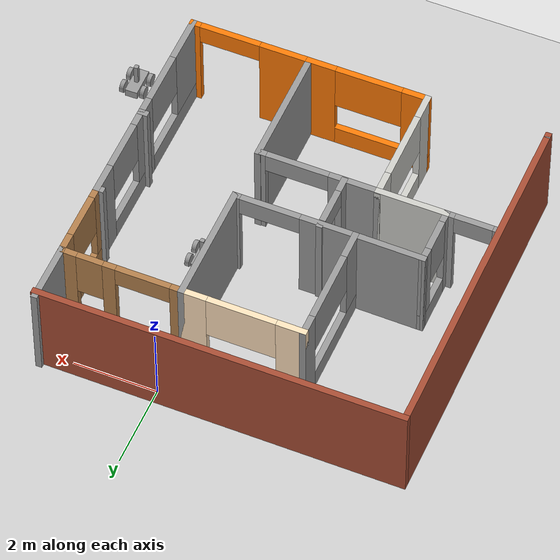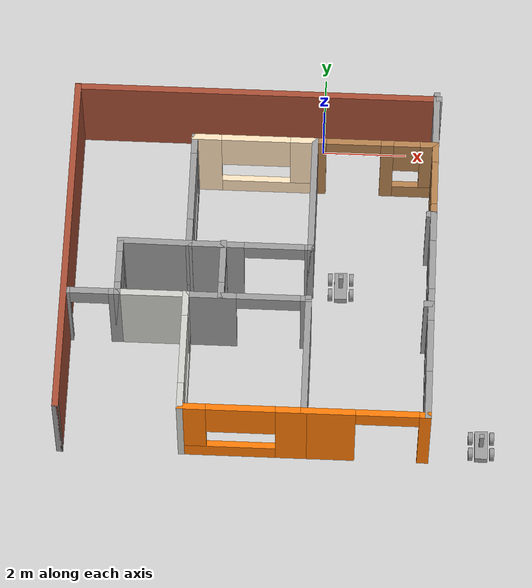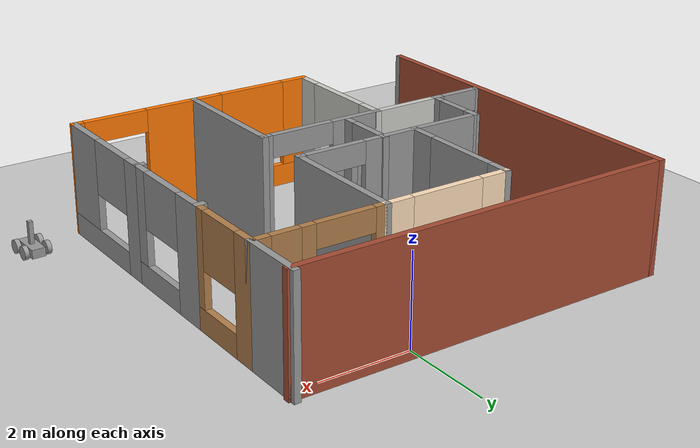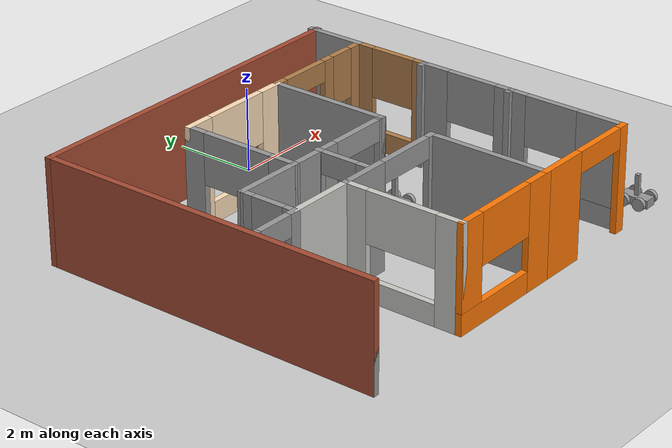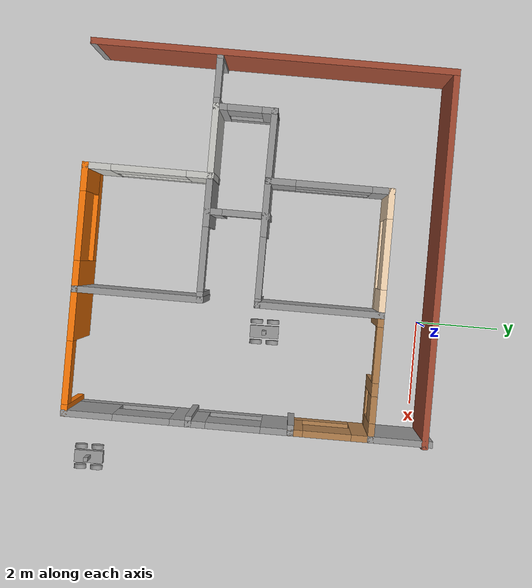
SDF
<sdf version="1.6">
 <world name="default">
  <plugin name="project_1_plugin" filename="libproject_1_plugin.so"/>
  <light name="sun" type="directional">
   <pose>0 0 10 0 -0 0</pose>
   <diffuse>0.8 0.8 0.8 1</diffuse>
   <specular>0.2 0.2 0.2 1</specular>
   <attenuation>
    <range>1000</range>
    <constant>0.9</constant>
    <linear>0.01</linear>
    <quadratic>0.001</quadratic>
   </attenuation>
   <direction>-0.5 0.1 -0.9</direction>
  </light>
  <model name="ground_plane">
   <static>1</static>
   <link name="link">
    <collision name="collision">
     <geometry><plane><normal>0 0 1</normal><size>100 100</size></plane></geometry>
     <surface>
      <contact><collide_bitmask>65535</collide_bitmask></contact>
      <friction><ode><mu>100</mu><mu2>50</mu2></ode></friction>
     </surface>
    </collision>
    <visual name="visual">
     <cast_shadows>0</cast_shadows>
     <geometry><plane><normal>0 0 1</normal><size>100 100</size></plane></geometry>
     <material>
      <script><uri>file://media/materials/scripts/gazebo.material</uri><name>Gazebo/Grey</name></script>
     </material>
    </visual>
   </link>
  </model>
  <gravity>0 0 -9.8</gravity>
  <magnetic_field>6e-06 2.3e-05 -4.2e-05</magnetic_field>
  <atmosphere type="adiabatic"/>
  <physics name="default_physics" default="0" type="ode">
   <max_step_size>0.001</max_step_size>
   <real_time_factor>1</real_time_factor>
   <real_time_update_rate>1000</real_time_update_rate>
  </physics>
  <scene><ambient>0.4 0.4 0.4 1</ambient><background>0.7 0.7 0.7 1</background><shadows>1</shadows></scene>
  <spherical_coordinates>
   <surface_model>EARTH_WGS84</surface_model>
   <latitude_deg>0</latitude_deg>
   <longitude_deg>0</longitude_deg>
   <elevation>0</elevation>
   <heading_deg>0</heading_deg>
  </spherical_coordinates>
  <model name="MyHome">
   <pose>-1.58 -3.915 0 0 -0 0</pose>
   <link name="Wall_0">
    <pose>-0.025 2.875 0 0 -0 0</pose>
    <visual name="Wall_0_Visual_0">
     <pose>-1.14611 0 1.25 0 -0 0</pose>
     <geometry><box><size>0.707769 0.15 2.5</size></box></geometry>
     <material>
      <script><uri>file://media/materials/scripts/gazebo.material</uri><name>Gazebo/Grey</name></script>
      <ambient>1 0.878431 0.733333 1</ambient>
     </material>
     <meta><layer>0</layer></meta>
    </visual>
    <collision name="Wall_0_Collision_0">
     <geometry><box><size>0.707769 0.15 2.5</size></box></geometry>
     <pose>-1.14611 0 1.25 0 -0 0</pose>
    </collision>
    <visual name="Wall_0_Visual_1">
     <pose>0.353885 0 0.25 0 -0 0</pose>
     <geometry><box><size>2.29223 0.15 0.5</size></box></geometry>
     <material>
      <script><uri>file://media/materials/scripts/gazebo.material</uri><name>Gazebo/Grey</name></script>
      <ambient>1 0.878431 0.733333 1</ambient>
     </material>
     <meta><layer>0</layer></meta>
    </visual>
    <collision name="Wall_0_Collision_1">
     <geometry><box><size>2.29223 0.15 0.5</size></box></geometry>
     <pose>0.353885 0 0.25 0 -0 0</pose>
    </collision>
    <visual name="Wall_0_Visual_2">
     <pose>1.16841 0 1.5 0 -0 0</pose>
     <geometry><box><size>0.663189 0.15 2</size></box></geometry>
     <material>
      <script><uri>file://media/materials/scripts/gazebo.material</uri><name>Gazebo/Grey</name></script>
      <ambient>1 0.878431 0.733333 1</ambient>
     </material>
     <meta><layer>0</layer></meta>
    </visual>
    <collision name="Wall_0_Collision_2">
     <geometry><box><size>0.663189 0.15 2</size></box></geometry>
     <pose>1.16841 0 1.5 0 -0 0</pose>
    </collision>
    <visual name="Wall_0_Visual_3">
     <pose>0.02229 0 1.9 0 -0 0</pose>
     <geometry><box><size>1.62904 0.15 1.2</size></box></geometry>
     <material>
      <script><uri>file://media/materials/scripts/gazebo.material</uri><name>Gazebo/Grey</name></script>
      <ambient>1 0.878431 0.733333 1</ambient>
     </material>
     <meta><layer>0</layer></meta>
    </visual>
    <collision name="Wall_0_Collision_3">
     <geometry><box><size>1.62904 0.15 1.2</size></box></geometry>
     <pose>0.02229 0 1.9 0 -0 0</pose>
    </collision>
   </link>
   <link name="Wall_11">
    <collision name="Wall_11_Collision">
     <geometry><box><size>0.25 0.15 2.5</size></box></geometry>
     <pose>0 0 1.25 0 -0 0</pose>
    </collision>
    <visual name="Wall_11_Visual">
     <pose>0 0 1.25 0 -0 0</pose>
     <geometry><box><size>0.25 0.15 2.5</size></box></geometry>
     <material>
      <script><uri>file://media/materials/scripts/gazebo.material</uri><name>Gazebo/Grey</name></script>
      <ambient>1 1 1 1</ambient>
     </material>
     <meta><layer>0</layer></meta>
    </visual>
    <pose>4.2 1.025 0 0 -0 3.14159</pose>
   </link>
   <link name="Wall_13">
    <pose>4.25 -0.15 0 0 0 -1.5708</pose>
    <visual name="Wall_13_Visual_0">
     <pose>-0.866536 0 1.25 0 -0 0</pose>
     <geometry><box><size>0.766927 0.15 2.5</size></box></geometry>
     <material>
      <script><uri>file://media/materials/scripts/gazebo.material</uri><name>Gazebo/Grey</name></script>
      <ambient>1 1 1 1</ambient>
     </material>
     <meta><layer>0</layer></meta>
    </visual>
    <collision name="Wall_13_Collision_0">
     <geometry><box><size>0.766927 0.15 2.5</size></box></geometry>
     <pose>-0.866536 0 1.25 0 -0 0</pose>
    </collision>
    <visual name="Wall_13_Visual_1">
     <pose>0.383464 0 0.25 0 -0 0</pose>
     <geometry><box><size>1.73307 0.15 0.5</size></box></geometry>
     <material>
      <script><uri>file://media/materials/scripts/gazebo.material</uri><name>Gazebo/Grey</name></script>
      <ambient>1 1 1 1</ambient>
     </material>
     <meta><layer>0</layer></meta>
    </visual>
    <collision name="Wall_13_Collision_1">
     <geometry><box><size>1.73307 0.15 0.5</size></box></geometry>
     <pose>0.383464 0 0.25 0 -0 0</pose>
    </collision>
    <visual name="Wall_13_Visual_2">
     <pose>1.01502 0 1.5 0 -0 0</pose>
     <geometry><box><size>0.469953 0.15 2</size></box></geometry>
     <material>
      <script><uri>file://media/materials/scripts/gazebo.material</uri><name>Gazebo/Grey</name></script>
      <ambient>1 1 1 1</ambient>
     </material>
     <meta><layer>0</layer></meta>
    </visual>
    <collision name="Wall_13_Collision_2">
     <geometry><box><size>0.469953 0.15 2</size></box></geometry>
     <pose>1.01502 0 1.5 0 -0 0</pose>
    </collision>
    <visual name="Wall_13_Visual_3">
     <pose>0.148487 0 1.9 0 -0 0</pose>
     <geometry><box><size>1.26312 0.15 1.2</size></box></geometry>
     <material>
      <script><uri>file://media/materials/scripts/gazebo.material</uri><name>Gazebo/Grey</name></script>
      <ambient>1 1 1 1</ambient>
     </material>
     <meta><layer>0</layer></meta>
    </visual>
    <collision name="Wall_13_Collision_3">
     <geometry><box><size>1.26312 0.15 1.2</size></box></geometry>
     <pose>0.148487 0 1.9 0 -0 0</pose>
    </collision>
   </link>
   <link name="Wall_14">
    <collision name="Wall_14_Collision">
     <geometry><box><size>0.25 0.15 2.5</size></box></geometry>
     <pose>0 0 1.25 0 -0 0</pose>
    </collision>
    <visual name="Wall_14_Visual">
     <pose>0 0 1.25 0 -0 0</pose>
     <geometry><box><size>0.25 0.15 2.5</size></box></geometry>
     <material>
      <script><uri>file://media/materials/scripts/gazebo.material</uri><name>Gazebo/Grey</name></script>
      <ambient>1 1 1 1</ambient>
     </material>
     <meta><layer>0</layer></meta>
    </visual>
    <pose>4.2 -1.325 0 0 -0 3.14159</pose>
   </link>
   <link name="Wall_16">
    <pose>4.25 -2.75 0 0 0 -1.5708</pose>
    <visual name="Wall_16_Visual_0">
     <pose>-1.24918 0 1.25 0 -0 0</pose>
     <geometry><box><size>0.501638 0.15 2.5</size></box></geometry>
     <material>
      <script><uri>file://media/materials/scripts/gazebo.material</uri><name>Gazebo/Grey</name></script>
      <ambient>1 1 1 1</ambient>
     </material>
     <meta><layer>0</layer></meta>
    </visual>
    <collision name="Wall_16_Collision_0">
     <geometry><box><size>0.501638 0.15 2.5</size></box></geometry>
     <pose>-1.24918 0 1.25 0 -0 0</pose>
    </collision>
    <visual name="Wall_16_Visual_1">
     <pose>0.250819 0 0.25 0 -0 0</pose>
     <geometry><box><size>2.49836 0.15 0.5</size></box></geometry>
     <material>
      <script><uri>file://media/materials/scripts/gazebo.material</uri><name>Gazebo/Grey</name></script>
      <ambient>1 1 1 1</ambient>
     </material>
     <meta><layer>0</layer></meta>
    </visual>
    <collision name="Wall_16_Collision_1">
     <geometry><box><size>2.49836 0.15 0.5</size></box></geometry>
     <pose>0.250819 0 0.25 0 -0 0</pose>
    </collision>
    <visual name="Wall_16_Visual_2">
     <pose>0.905819 0 1.5 0 -0 0</pose>
     <geometry><box><size>1.18836 0.15 2</size></box></geometry>
     <material>
      <script><uri>file://media/materials/scripts/gazebo.material</uri><name>Gazebo/Grey</name></script>
      <ambient>1 1 1 1</ambient>
     </material>
     <meta><layer>0</layer></meta>
    </visual>
    <collision name="Wall_16_Collision_2">
     <geometry><box><size>1.18836 0.15 2</size></box></geometry>
     <pose>0.905819 0 1.5 0 -0 0</pose>
    </collision>
    <visual name="Wall_16_Visual_3">
     <pose>-0.343362 0 1.9 0 -0 0</pose>
     <geometry><box><size>1.31 0.15 1.2</size></box></geometry>
     <material>
      <script><uri>file://media/materials/scripts/gazebo.material</uri><name>Gazebo/Grey</name></script>
      <ambient>1 1 1 1</ambient>
     </material>
     <meta><layer>0</layer></meta>
    </visual>
    <collision name="Wall_16_Collision_3">
     <geometry><box><size>1.31 0.15 1.2</size></box></geometry>
     <pose>-0.343362 0 1.9 0 -0 0</pose>
    </collision>
   </link>
   <link name="Wall_18">
    <pose>2.825 -4.175 0 0 -0 3.14159</pose>
    <visual name="Wall_18_Visual_0">
     <pose>-1.36366 0 1.25 0 -0 0</pose>
     <geometry><box><size>0.272669 0.15 2.5</size></box></geometry>
     <material>
      <script><uri>file://media/materials/scripts/gazebo.material</uri><name>Gazebo/Grey</name></script>
      <ambient>0.996078 0.47451 0.0196078 1</ambient>
     </material>
     <meta><layer>0</layer></meta>
    </visual>
    <collision name="Wall_18_Collision_0">
     <geometry><box><size>0.272669 0.15 2.5</size></box></geometry>
     <pose>-1.36366 0 1.25 0 -0 0</pose>
    </collision>
    <visual name="Wall_18_Visual_1">
     <pose>0.866335 0 1.25 0 -0 0</pose>
     <geometry><box><size>1.26733 0.15 2.5</size></box></geometry>
     <material>
      <script><uri>file://media/materials/scripts/gazebo.material</uri><name>Gazebo/Grey</name></script>
      <ambient>0.996078 0.47451 0.0196078 1</ambient>
     </material>
     <meta><layer>0</layer></meta>
    </visual>
    <collision name="Wall_18_Collision_1">
     <geometry><box><size>1.26733 0.15 2.5</size></box></geometry>
     <pose>0.866335 0 1.25 0 -0 0</pose>
    </collision>
    <visual name="Wall_18_Visual_2">
     <pose>-0.497331 0 2.25 0 -0 0</pose>
     <geometry><box><size>1.46 0.15 0.5</size></box></geometry>
     <material>
      <script><uri>file://media/materials/scripts/gazebo.material</uri><name>Gazebo/Grey</name></script>
      <ambient>0.996078 0.47451 0.0196078 1</ambient>
     </material>
     <meta><layer>0</layer></meta>
    </visual>
    <collision name="Wall_18_Collision_2">
     <geometry><box><size>1.46 0.15 0.5</size></box></geometry>
     <pose>-0.497331 0 2.25 0 -0 0</pose>
    </collision>
   </link>
   <link name="Wall_2">
    <pose>-1.45 1.45 0 0 0 -1.5708</pose>
    <visual name="Wall_2_Visual_0">
     <pose>-1.23642 0 1.25 0 -0 0</pose>
     <geometry><box><size>0.527169 0.15 2.5</size></box></geometry>
     <material>
      <script><uri>file://media/materials/scripts/gazebo.material</uri><name>Gazebo/Grey</name></script>
      <ambient>0.529412 0.529412 0.529412 1</ambient>
     </material>
     <meta><layer>0</layer></meta>
    </visual>
    <collision name="Wall_2_Collision_0">
     <geometry><box><size>0.527169 0.15 2.5</size></box></geometry>
     <pose>-1.23642 0 1.25 0 -0 0</pose>
    </collision>
    <visual name="Wall_2_Visual_1">
     <pose>0.263585 0 0.25 0 -0 0</pose>
     <geometry><box><size>2.47283 0.15 0.5</size></box></geometry>
     <material>
      <script><uri>file://media/materials/scripts/gazebo.material</uri><name>Gazebo/Grey</name></script>
      <ambient>0.529412 0.529412 0.529412 1</ambient>
     </material>
     <meta><layer>0</layer></meta>
    </visual>
    <collision name="Wall_2_Collision_1">
     <geometry><box><size>2.47283 0.15 0.5</size></box></geometry>
     <pose>0.263585 0 0.25 0 -0 0</pose>
    </collision>
    <visual name="Wall_2_Visual_2">
     <pose>1.14386 0 1.5 0 -0 0</pose>
     <geometry><box><size>0.712285 0.15 2</size></box></geometry>
     <material>
      <script><uri>file://media/materials/scripts/gazebo.material</uri><name>Gazebo/Grey</name></script>
      <ambient>0.529412 0.529412 0.529412 1</ambient>
     </material>
     <meta><layer>0</layer></meta>
    </visual>
    <collision name="Wall_2_Collision_2">
     <geometry><box><size>0.712285 0.15 2</size></box></geometry>
     <pose>1.14386 0 1.5 0 -0 0</pose>
    </collision>
    <visual name="Wall_2_Visual_3">
     <pose>-0.092558 0 1.9 0 -0 0</pose>
     <geometry><box><size>1.76055 0.15 1.2</size></box></geometry>
     <material>
      <script><uri>file://media/materials/scripts/gazebo.material</uri><name>Gazebo/Grey</name></script>
      <ambient>0.529412 0.529412 0.529412 1</ambient>
     </material>
     <meta><layer>0</layer></meta>
    </visual>
    <collision name="Wall_2_Collision_3">
     <geometry><box><size>1.76055 0.15 1.2</size></box></geometry>
     <pose>-0.092558 0 1.9 0 -0 0</pose>
    </collision>
   </link>
   <link name="Wall_20">
    <collision name="Wall_20_Collision">
     <geometry><box><size>0.15 0.15 2.5</size></box></geometry>
     <pose>0 0 1.25 0 -0 0</pose>
    </collision>
    <visual name="Wall_20_Visual">
     <pose>0 0 1.25 0 -0 0</pose>
     <geometry><box><size>0.15 0.15 2.5</size></box></geometry>
     <material>
      <script><uri>file://media/materials/scripts/gazebo.material</uri><name>Gazebo/Grey</name></script>
      <ambient>1 1 1 1</ambient>
     </material>
     <meta><layer>0</layer></meta>
    </visual>
    <pose>1.4 -4.175 0 0 -0 0</pose>
   </link>
   <link name="Wall_22">
    <pose>-0.025 -4.175 0 0 -0 3.14159</pose>
    <visual name="Wall_22_Visual_0">
     <pose>-1.13467 0 1.25 0 -0 0</pose>
     <geometry><box><size>0.73066 0.15 2.5</size></box></geometry>
     <material>
      <script><uri>file://media/materials/scripts/gazebo.material</uri><name>Gazebo/Grey</name></script>
      <ambient>0.996078 0.47451 0.0196078 1</ambient>
     </material>
     <meta><layer>0</layer></meta>
    </visual>
    <collision name="Wall_22_Collision_0">
     <geometry><box><size>0.73066 0.15 2.5</size></box></geometry>
     <pose>-1.13467 0 1.25 0 -0 0</pose>
    </collision>
    <visual name="Wall_22_Visual_1">
     <pose>0.36533 0 0.25 0 -0 0</pose>
     <geometry><box><size>2.26934 0.15 0.5</size></box></geometry>
     <material>
      <script><uri>file://media/materials/scripts/gazebo.material</uri><name>Gazebo/Grey</name></script>
      <ambient>0.996078 0.47451 0.0196078 1</ambient>
     </material>
     <meta><layer>0</layer></meta>
    </visual>
    <collision name="Wall_22_Collision_1">
     <geometry><box><size>2.26934 0.15 0.5</size></box></geometry>
     <pose>0.36533 0 0.25 0 -0 0</pose>
    </collision>
    <visual name="Wall_22_Visual_2">
     <pose>1.16533 0 1.5 0 -0 0</pose>
     <geometry><box><size>0.66934 0.15 2</size></box></geometry>
     <material>
      <script><uri>file://media/materials/scripts/gazebo.material</uri><name>Gazebo/Grey</name></script>
      <ambient>0.996078 0.47451 0.0196078 1</ambient>
     </material>
     <meta><layer>0</layer></meta>
    </visual>
    <collision name="Wall_22_Collision_2">
     <geometry><box><size>0.66934 0.15 2</size></box></geometry>
     <pose>1.16533 0 1.5 0 -0 0</pose>
    </collision>
    <visual name="Wall_22_Visual_3">
     <pose>0.03066 0 1.9 0 -0 0</pose>
     <geometry><box><size>1.6 0.15 1.2</size></box></geometry>
     <material>
      <script><uri>file://media/materials/scripts/gazebo.material</uri><name>Gazebo/Grey</name></script>
      <ambient>0.996078 0.47451 0.0196078 1</ambient>
     </material>
     <meta><layer>0</layer></meta>
    </visual>
    <collision name="Wall_22_Collision_3">
     <geometry><box><size>1.6 0.15 1.2</size></box></geometry>
     <pose>0.03066 0 1.9 0 -0 0</pose>
    </collision>
   </link>
   <link name="Wall_24">
    <pose>-1.45 -2.73479 0 0 -0 1.5708</pose>
    <visual name="Wall_24_Visual_0">
     <pose>-1.18374 0 1.25 0 -0 0</pose>
     <geometry><box><size>0.662934 0.15 2.5</size></box></geometry>
     <material>
      <script><uri>file://media/materials/scripts/gazebo.material</uri><name>Gazebo/CeilingTiled</name></script>
      <ambient>1 1 1 1</ambient>
     </material>
     <meta><layer>0</layer></meta>
    </visual>
    <collision name="Wall_24_Collision_0">
     <geometry><box><size>0.662934 0.15 2.5</size></box></geometry>
     <pose>-1.18374 0 1.25 0 -0 0</pose>
    </collision>
    <visual name="Wall_24_Visual_1">
     <pose>0.331467 0 0.25 0 -0 0</pose>
     <geometry><box><size>2.36748 0.15 0.5</size></box></geometry>
     <material>
      <script><uri>file://media/materials/scripts/gazebo.material</uri><name>Gazebo/CeilingTiled</name></script>
      <ambient>1 1 1 1</ambient>
     </material>
     <meta><layer>0</layer></meta>
    </visual>
    <collision name="Wall_24_Collision_1">
     <geometry><box><size>2.36748 0.15 0.5</size></box></geometry>
     <pose>0.331467 0 0.25 0 -0 0</pose>
    </collision>
    <visual name="Wall_24_Visual_2">
     <pose>1.19647 0 1.5 0 -0 0</pose>
     <geometry><box><size>0.637483 0.15 2</size></box></geometry>
     <material>
      <script><uri>file://media/materials/scripts/gazebo.material</uri><name>Gazebo/CeilingTiled</name></script>
      <ambient>1 1 1 1</ambient>
     </material>
     <meta><layer>0</layer></meta>
    </visual>
    <collision name="Wall_24_Collision_2">
     <geometry><box><size>0.637483 0.15 2</size></box></geometry>
     <pose>1.19647 0 1.5 0 -0 0</pose>
    </collision>
    <visual name="Wall_24_Visual_3">
     <pose>0.012725 0 1.9 0 -0 0</pose>
     <geometry><box><size>1.73 0.15 1.2</size></box></geometry>
     <material>
      <script><uri>file://media/materials/scripts/gazebo.material</uri><name>Gazebo/CeilingTiled</name></script>
      <ambient>1 1 1 1</ambient>
     </material>
     <meta><layer>0</layer></meta>
    </visual>
    <collision name="Wall_24_Collision_3">
     <geometry><box><size>1.73 0.15 1.2</size></box></geometry>
     <pose>0.012725 0 1.9 0 -0 0</pose>
    </collision>
   </link>
   <link name="Wall_25">
    <collision name="Wall_25_Collision">
     <geometry><box><size>0.15 0.15 2.5</size></box></geometry>
     <pose>0 0 1.25 0 -0 0</pose>
    </collision>
    <visual name="Wall_25_Visual">
     <pose>0 0 1.25 0 -0 0</pose>
     <geometry><box><size>0.15 0.15 2.5</size></box></geometry>
     <material>
      <script><uri>file://media/materials/scripts/gazebo.material</uri><name>Gazebo/Grey</name></script>
      <ambient>1 1 1 1</ambient>
     </material>
     <meta><layer>0</layer></meta>
    </visual>
    <pose>-1.45 -1.29458 0 0 -0 0</pose>
   </link>
   <link name="Wall_26">
    <pose>-0.025 -1.30979 0 0 -0 0</pose>
    <visual name="Wall_26_Visual_0">
     <pose>-0.875794 0 1.25 0 -0 0</pose>
     <geometry><box><size>1.24841 0.15 2.5</size></box></geometry>
     <material>
      <script><uri>file://media/materials/scripts/gazebo.material</uri><name>Gazebo/Grey</name></script>
      <ambient>1 1 1 1</ambient>
     </material>
     <meta><layer>0</layer></meta>
    </visual>
    <collision name="Wall_26_Collision_0">
     <geometry><box><size>1.24841 0.15 2.5</size></box></geometry>
     <pose>-0.875794 0 1.25 0 -0 0</pose>
    </collision>
    <visual name="Wall_26_Visual_1">
     <pose>1.36921 0 1.25 0 -0 0</pose>
     <geometry><box><size>0.261588 0.15 2.5</size></box></geometry>
     <material>
      <script><uri>file://media/materials/scripts/gazebo.material</uri><name>Gazebo/Grey</name></script>
      <ambient>1 1 1 1</ambient>
     </material>
     <meta><layer>0</layer></meta>
    </visual>
    <collision name="Wall_26_Collision_1">
     <geometry><box><size>0.261588 0.15 2.5</size></box></geometry>
     <pose>1.36921 0 1.25 0 -0 0</pose>
    </collision>
    <visual name="Wall_26_Visual_2">
     <pose>0.493412 0 2.25 0 -0 0</pose>
     <geometry><box><size>1.49 0.15 0.5</size></box></geometry>
     <material>
      <script><uri>file://media/materials/scripts/gazebo.material</uri><name>Gazebo/Grey</name></script>
      <ambient>1 1 1 1</ambient>
     </material>
     <meta><layer>0</layer></meta>
    </visual>
    <collision name="Wall_26_Collision_2">
     <geometry><box><size>1.49 0.15 0.5</size></box></geometry>
     <pose>0.493412 0 2.25 0 -0 0</pose>
    </collision>
   </link>
   <link name="Wall_27">
    <collision name="Wall_27_Collision">
     <geometry><box><size>3.03042 0.15 2.5</size></box></geometry>
     <pose>0 0 1.25 0 -0 0</pose>
    </collision>
    <visual name="Wall_27_Visual">
     <pose>0 0 1.25 0 -0 0</pose>
     <geometry><box><size>3.03042 0.15 2.5</size></box></geometry>
     <material>
      <script><uri>file://media/materials/scripts/gazebo.material</uri><name>Gazebo/Grey</name></script>
      <ambient>1 1 1 1</ambient>
     </material>
     <meta><layer>0</layer></meta>
    </visual>
    <pose>1.4 -2.73479 0 0 0 -1.5708</pose>
   </link>
   <link name="Wall_3">
    <pose>-0.025 0.025 0 0 -0 0</pose>
    <visual name="Wall_3_Visual_0">
     <pose>-0.816671 0 1.25 0 -0 0</pose>
     <geometry><box><size>1.36666 0.15 2.5</size></box></geometry>
     <material>
      <script><uri>file://media/materials/scripts/gazebo.material</uri><name>Gazebo/Grey</name></script>
      <ambient>1 1 1 1</ambient>
     </material>
     <meta><layer>0</layer></meta>
    </visual>
    <collision name="Wall_3_Collision_0">
     <geometry><box><size>1.36666 0.15 2.5</size></box></geometry>
     <pose>-0.816671 0 1.25 0 -0 0</pose>
    </collision>
    <visual name="Wall_3_Visual_1">
     <pose>1.39333 0 1.25 0 -0 0</pose>
     <geometry><box><size>0.213342 0.15 2.5</size></box></geometry>
     <material>
      <script><uri>file://media/materials/scripts/gazebo.material</uri><name>Gazebo/Grey</name></script>
      <ambient>1 1 1 1</ambient>
     </material>
     <meta><layer>0</layer></meta>
    </visual>
    <collision name="Wall_3_Collision_1">
     <geometry><box><size>0.213342 0.15 2.5</size></box></geometry>
     <pose>1.39333 0 1.25 0 -0 0</pose>
    </collision>
    <visual name="Wall_3_Visual_2">
     <pose>0.576658 0 2.25 0 -0 0</pose>
     <geometry><box><size>1.42 0.15 0.5</size></box></geometry>
     <material>
      <script><uri>file://media/materials/scripts/gazebo.material</uri><name>Gazebo/Grey</name></script>
      <ambient>1 1 1 1</ambient>
     </material>
     <meta><layer>0</layer></meta>
    </visual>
    <collision name="Wall_3_Collision_2">
     <geometry><box><size>1.42 0.15 0.5</size></box></geometry>
     <pose>0.576658 0 2.25 0 -0 0</pose>
    </collision>
   </link>
   <link name="Wall_35">
    <collision name="Wall_35_Collision">
     <geometry><box><size>1.75 0.15 2.5</size></box></geometry>
     <pose>0 0 1.25 0 -0 0</pose>
    </collision>
    <visual name="Wall_35_Visual">
     <pose>0 0 1.25 0 -0 0</pose>
     <geometry><box><size>1.75 0.15 2.5</size></box></geometry>
     <material>
      <script><uri>file://media/materials/scripts/gazebo.material</uri><name>Gazebo/CeilingTiled</name></script>
      <ambient>1 1 1 1</ambient>
     </material>
     <meta><layer>0</layer></meta>
    </visual>
    <pose>-2.25 -1.30979 0 0 -0 3.14159</pose>
   </link>
   <link name="Wall_36">
    <pose>-3.05 -0.634791 0 0 -0 1.5708</pose>
    <visual name="Wall_36_Visual_0">
     <pose>-0.584129 0 1.25 0 -0 0</pose>
     <geometry><box><size>0.331742 0.15 2.5</size></box></geometry>
     <material>
      <script><uri>file://media/materials/scripts/gazebo.material</uri><name>Gazebo/Grey</name></script>
      <ambient>1 1 1 1</ambient>
     </material>
     <meta><layer>0</layer></meta>
    </visual>
    <collision name="Wall_36_Collision_0">
     <geometry><box><size>0.331742 0.15 2.5</size></box></geometry>
     <pose>-0.584129 0 1.25 0 -0 0</pose>
    </collision>
    <visual name="Wall_36_Visual_1">
     <pose>0.165871 0 0.25 0 -0 0</pose>
     <geometry><box><size>1.16826 0.15 0.5</size></box></geometry>
     <material>
      <script><uri>file://media/materials/scripts/gazebo.material</uri><name>Gazebo/Grey</name></script>
      <ambient>1 1 1 1</ambient>
     </material>
     <meta><layer>0</layer></meta>
    </visual>
    <collision name="Wall_36_Collision_1">
     <geometry><box><size>1.16826 0.15 0.5</size></box></geometry>
     <pose>0.165871 0 0.25 0 -0 0</pose>
    </collision>
    <visual name="Wall_36_Visual_2">
     <pose>0.565871 0 1.5 0 -0 0</pose>
     <geometry><box><size>0.368258 0.15 2</size></box></geometry>
     <material>
      <script><uri>file://media/materials/scripts/gazebo.material</uri><name>Gazebo/Grey</name></script>
      <ambient>1 1 1 1</ambient>
     </material>
     <meta><layer>0</layer></meta>
    </visual>
    <collision name="Wall_36_Collision_2">
     <geometry><box><size>0.368258 0.15 2</size></box></geometry>
     <pose>0.565871 0 1.5 0 -0 0</pose>
    </collision>
    <visual name="Wall_36_Visual_3">
     <pose>-0.018258 0 1.9 0 -0 0</pose>
     <geometry><box><size>0.8 0.15 1.2</size></box></geometry>
     <material>
      <script><uri>file://media/materials/scripts/gazebo.material</uri><name>Gazebo/Grey</name></script>
      <ambient>1 1 1 1</ambient>
     </material>
     <meta><layer>0</layer></meta>
    </visual>
    <collision name="Wall_36_Collision_3">
     <geometry><box><size>0.8 0.15 1.2</size></box></geometry>
     <pose>-0.018258 0 1.9 0 -0 0</pose>
    </collision>
   </link>
   <link name="Wall_38">
    <collision name="Wall_38_Collision">
     <geometry><box><size>1.75 0.15 2.5</size></box></geometry>
     <pose>0 0 1.25 0 -0 0</pose>
    </collision>
    <visual name="Wall_38_Visual">
     <pose>0 0 1.25 0 -0 0</pose>
     <geometry><box><size>1.75 0.15 2.5</size></box></geometry>
     <material>
      <script><uri>file://media/materials/scripts/gazebo.material</uri><name>Gazebo/Grey</name></script>
      <ambient>1 1 1 1</ambient>
     </material>
     <meta><layer>0</layer></meta>
    </visual>
    <pose>-2.25 0.032605 0 0 -0 3.13209</pose>
   </link>
   <link name="Wall_4">
    <collision name="Wall_4_Collision">
     <geometry><box><size>0.15 0.15 2.5</size></box></geometry>
     <pose>0 0 1.25 0 -0 0</pose>
    </collision>
    <visual name="Wall_4_Visual">
     <pose>0 0 1.25 0 -0 0</pose>
     <geometry><box><size>0.15 0.15 2.5</size></box></geometry>
     <material>
      <script><uri>file://media/materials/scripts/gazebo.material</uri><name>Gazebo/Grey</name></script>
      <ambient>1 1 1 1</ambient>
     </material>
     <meta><layer>0</layer></meta>
    </visual>
    <pose>1.4 0.025 0 0 -0 0</pose>
   </link>
   <link name="Wall_40">
    <pose>-0.639821 -0.613584 0 0 0 -1.5708</pose>
    <visual name="Wall_40_Visual_0">
     <pose>-0.650543 0 1.25 0 -0 0</pose>
     <geometry><box><size>0.198913 0.15 2.5</size></box></geometry>
     <material>
      <script><uri>file://media/materials/scripts/gazebo.material</uri><name>Gazebo/Grey</name></script>
      <ambient>1 1 1 1</ambient>
     </material>
     <meta><layer>0</layer></meta>
    </visual>
    <collision name="Wall_40_Collision_0">
     <geometry><box><size>0.198913 0.15 2.5</size></box></geometry>
     <pose>-0.650543 0 1.25 0 -0 0</pose>
    </collision>
    <visual name="Wall_40_Visual_1">
     <pose>0.549457 0 1.25 0 -0 0</pose>
     <geometry><box><size>0.401087 0.15 2.5</size></box></geometry>
     <material>
      <script><uri>file://media/materials/scripts/gazebo.material</uri><name>Gazebo/Grey</name></script>
      <ambient>1 1 1 1</ambient>
     </material>
     <meta><layer>0</layer></meta>
    </visual>
    <collision name="Wall_40_Collision_1">
     <geometry><box><size>0.401087 0.15 2.5</size></box></geometry>
     <pose>0.549457 0 1.25 0 -0 0</pose>
    </collision>
    <visual name="Wall_40_Visual_2">
     <pose>-0.101087 0 2.25 0 -0 0</pose>
     <geometry><box><size>0.9 0.15 0.5</size></box></geometry>
     <material>
      <script><uri>file://media/materials/scripts/gazebo.material</uri><name>Gazebo/Grey</name></script>
      <ambient>1 1 1 1</ambient>
     </material>
     <meta><layer>0</layer></meta>
    </visual>
    <collision name="Wall_40_Collision_2">
     <geometry><box><size>0.9 0.15 0.5</size></box></geometry>
     <pose>-0.101087 0 2.25 0 -0 0</pose>
    </collision>
   </link>
   <link name="Wall_45">
    <collision name="Wall_45_Collision">
     <geometry><box><size>8.5 0.15 2.5</size></box></geometry>
     <pose>0 0 1.25 0 -0 0</pose>
    </collision>
    <visual name="Wall_45_Visual">
     <pose>0 0 1.25 0 -0 0</pose>
     <geometry><box><size>8.5 0.15 2.5</size></box></geometry>
     <material>
      <script><uri>file://media/materials/scripts/gazebo.material</uri><name>Gazebo/Bricks</name></script>
      <ambient>1 1 1 1</ambient>
     </material>
     <meta><layer>0</layer></meta>
    </visual>
    <pose>-4.3 -0.05 0 0 0 -1.5708</pose>
   </link>
   <link name="Wall_46">
    <collision name="Wall_46_Collision">
     <geometry><box><size>0.15 0.15 2.5</size></box></geometry>
     <pose>0 0 1.25 0 -0 0</pose>
    </collision>
    <visual name="Wall_46_Visual">
     <pose>0 0 1.25 0 -0 0</pose>
     <geometry><box><size>0.15 0.15 2.5</size></box></geometry>
     <material>
      <script><uri>file://media/materials/scripts/gazebo.material</uri><name>Gazebo/Grey</name></script>
      <ambient>1 1 1 1</ambient>
     </material>
     <meta><layer>0</layer></meta>
    </visual>
    <pose>-4.3 -4.225 0 0 -0 0</pose>
   </link>
   <link name="Wall_49">
    <pose>-3.6 -1.30979 0 0 -0 3.14159</pose>
    <visual name="Wall_49_Visual_0">
     <pose>-0.48744 0 1.25 0 -0 0</pose>
     <geometry><box><size>0.27512 0.15 2.5</size></box></geometry>
     <material>
      <script><uri>file://media/materials/scripts/gazebo.material</uri><name>Gazebo/Grey</name></script>
      <ambient>1 1 1 1</ambient>
     </material>
     <meta><layer>0</layer></meta>
    </visual>
    <collision name="Wall_49_Collision_0">
     <geometry><box><size>0.27512 0.15 2.5</size></box></geometry>
     <pose>-0.48744 0 1.25 0 -0 0</pose>
    </collision>
    <visual name="Wall_49_Visual_1">
     <pose>0.58756 0 1.25 0 -0 0</pose>
     <geometry><box><size>0.07488 0.15 2.5</size></box></geometry>
     <material>
      <script><uri>file://media/materials/scripts/gazebo.material</uri><name>Gazebo/Grey</name></script>
      <ambient>1 1 1 1</ambient>
     </material>
     <meta><layer>0</layer></meta>
    </visual>
    <collision name="Wall_49_Collision_1">
     <geometry><box><size>0.07488 0.15 2.5</size></box></geometry>
     <pose>0.58756 0 1.25 0 -0 0</pose>
    </collision>
    <visual name="Wall_49_Visual_2">
     <pose>0.10012 0 2.25 0 -0 0</pose>
     <geometry><box><size>0.9 0.15 0.5</size></box></geometry>
     <material>
      <script><uri>file://media/materials/scripts/gazebo.material</uri><name>Gazebo/Grey</name></script>
      <ambient>1 1 1 1</ambient>
     </material>
     <meta><layer>0</layer></meta>
    </visual>
    <collision name="Wall_49_Collision_2">
     <geometry><box><size>0.9 0.15 0.5</size></box></geometry>
     <pose>0.10012 0 2.25 0 -0 0</pose>
    </collision>
   </link>
   <link name="Wall_5">
    <collision name="Wall_5_Collision">
     <geometry><box><size>3 0.15 2.5</size></box></geometry>
     <pose>0 0 1.25 0 -0 0</pose>
    </collision>
    <visual name="Wall_5_Visual">
     <pose>0 0 1.25 0 -0 0</pose>
     <geometry><box><size>3 0.15 2.5</size></box></geometry>
     <material>
      <script><uri>file://media/materials/scripts/gazebo.material</uri><name>Gazebo/Grey</name></script>
      <ambient>0.529412 0.529412 0.529412 1</ambient>
     </material>
     <meta><layer>0</layer></meta>
    </visual>
    <pose>1.4 1.45 0 0 -0 1.5708</pose>
   </link>
   <link name="Wall_52">
    <collision name="Wall_52_Collision">
     <geometry><box><size>8.75 0.15 2.5</size></box></geometry>
     <pose>0 0 1.25 0 -0 0</pose>
    </collision>
    <visual name="Wall_52_Visual">
     <pose>0 0 1.25 0 -0 0</pose>
     <geometry><box><size>8.75 0.15 2.5</size></box></geometry>
     <material>
      <script><uri>file://media/materials/scripts/gazebo.material</uri><name>Gazebo/Bricks</name></script>
      <ambient>1 1 1 1</ambient>
     </material>
     <meta><layer>0</layer></meta>
    </visual>
    <pose>0 4.125 0 0 -0 0</pose>
   </link>
   <link name="Wall_53">
    <collision name="Wall_53_Collision">
     <geometry><box><size>0.15 0.15 2.5</size></box></geometry>
     <pose>0 0 1.25 0 -0 0</pose>
    </collision>
    <visual name="Wall_53_Visual">
     <pose>0 0 1.25 0 -0 0</pose>
     <geometry><box><size>0.15 0.15 2.5</size></box></geometry>
     <material>
      <script><uri>file://media/materials/scripts/gazebo.material</uri><name>Gazebo/Grey</name></script>
      <ambient>1 1 1 1</ambient>
     </material>
     <meta><layer>0</layer></meta>
    </visual>
    <pose>4.3 4.125 0 0 -0 0</pose>
   </link>
   <link name="Wall_55">
    <collision name="Wall_55_Collision">
     <geometry><box><size>1.5 0.15 2.5</size></box></geometry>
     <pose>0 0 1.25 0 -0 0</pose>
    </collision>
    <visual name="Wall_55_Visual">
     <pose>0 0 1.25 0 -0 0</pose>
     <geometry><box><size>1.5 0.15 2.5</size></box></geometry>
     <material>
      <script><uri>file://media/materials/scripts/gazebo.material</uri><name>Gazebo/Grey</name></script>
      <ambient>1 1 1 1</ambient>
     </material>
     <meta><layer>0</layer></meta>
    </visual>
    <pose>4.25 3.55 0 0 -0 1.5708</pose>
   </link>
   <link name="Wall_7">
    <pose>2.825 2.875 0 0 -0 0</pose>
    <visual name="Wall_7_Visual_0">
     <pose>-1.32901 0 1.25 0 -0 0</pose>
     <geometry><box><size>0.341972 0.15 2.5</size></box></geometry>
     <material>
      <script><uri>file://media/materials/scripts/gazebo.material</uri><name>Gazebo/Wood</name></script>
      <ambient>1 1 1 1</ambient>
     </material>
     <meta><layer>0</layer></meta>
    </visual>
    <collision name="Wall_7_Collision_0">
     <geometry><box><size>0.341972 0.15 2.5</size></box></geometry>
     <pose>-1.32901 0 1.25 0 -0 0</pose>
    </collision>
    <visual name="Wall_7_Visual_1">
     <pose>0.283413 0 1.25 0 -0 0</pose>
     <geometry><box><size>0.302883 0.15 2.5</size></box></geometry>
     <material>
      <script><uri>file://media/materials/scripts/gazebo.material</uri><name>Gazebo/Wood</name></script>
      <ambient>1 1 1 1</ambient>
     </material>
     <meta><layer>0</layer></meta>
    </visual>
    <collision name="Wall_7_Collision_1">
     <geometry><box><size>0.302883 0.15 2.5</size></box></geometry>
     <pose>0.283413 0 1.25 0 -0 0</pose>
    </collision>
    <visual name="Wall_7_Visual_2">
     <pose>0.967427 0 0.25 0 -0 0</pose>
     <geometry><box><size>1.06515 0.15 0.5</size></box></geometry>
     <material>
      <script><uri>file://media/materials/scripts/gazebo.material</uri><name>Gazebo/Wood</name></script>
      <ambient>1 1 1 1</ambient>
     </material>
     <meta><layer>0</layer></meta>
    </visual>
    <collision name="Wall_7_Collision_2">
     <geometry><box><size>1.06515 0.15 0.5</size></box></geometry>
     <pose>0.967427 0 0.25 0 -0 0</pose>
    </collision>
    <visual name="Wall_7_Visual_3">
     <pose>1.27892 0 1.5 0 -0 0</pose>
     <geometry><box><size>0.442161 0.15 2</size></box></geometry>
     <material>
      <script><uri>file://media/materials/scripts/gazebo.material</uri><name>Gazebo/Wood</name></script>
      <ambient>1 1 1 1</ambient>
     </material>
     <meta><layer>0</layer></meta>
    </visual>
    <collision name="Wall_7_Collision_3">
     <geometry><box><size>0.442161 0.15 2</size></box></geometry>
     <pose>1.27892 0 1.5 0 -0 0</pose>
    </collision>
    <visual name="Wall_7_Visual_4">
     <pose>0.746347 0 1.9 0 -0 0</pose>
     <geometry><box><size>0.622984 0.15 1.2</size></box></geometry>
     <material>
      <script><uri>file://media/materials/scripts/gazebo.material</uri><name>Gazebo/Wood</name></script>
      <ambient>1 1 1 1</ambient>
     </material>
     <meta><layer>0</layer></meta>
    </visual>
    <collision name="Wall_7_Collision_4">
     <geometry><box><size>0.622984 0.15 1.2</size></box></geometry>
     <pose>0.746347 0 1.9 0 -0 0</pose>
    </collision>
    <visual name="Wall_7_Visual_5">
     <pose>-0.513028 0 2.25 0 -0 0</pose>
     <geometry><box><size>1.29 0.15 0.5</size></box></geometry>
     <material>
      <script><uri>file://media/materials/scripts/gazebo.material</uri><name>Gazebo/Wood</name></script>
      <ambient>1 1 1 1</ambient>
     </material>
     <meta><layer>0</layer></meta>
    </visual>
    <collision name="Wall_7_Collision_5">
     <geometry><box><size>1.29 0.15 0.5</size></box></geometry>
     <pose>-0.513028 0 2.25 0 -0 0</pose>
    </collision>
   </link>
   <link name="Wall_9">
    <pose>4.25 1.95 0 0 0 -1.5708</pose>
    <visual name="Wall_9_Visual_0">
     <pose>-0.736845 0 1.25 0 -0 0</pose>
     <geometry><box><size>0.526309 0.15 2.5</size></box></geometry>
     <material>
      <script><uri>file://media/materials/scripts/gazebo.material</uri><name>Gazebo/Wood</name></script>
      <ambient>1 1 1 1</ambient>
     </material>
     <meta><layer>0</layer></meta>
    </visual>
    <collision name="Wall_9_Collision_0">
     <geometry><box><size>0.526309 0.15 2.5</size></box></geometry>
     <pose>-0.736845 0 1.25 0 -0 0</pose>
    </collision>
    <visual name="Wall_9_Visual_1">
     <pose>0.263155 0 0.25 0 -0 0</pose>
     <geometry><box><size>1.47369 0.15 0.5</size></box></geometry>
     <material>
      <script><uri>file://media/materials/scripts/gazebo.material</uri><name>Gazebo/Wood</name></script>
      <ambient>1 1 1 1</ambient>
     </material>
     <meta><layer>0</layer></meta>
    </visual>
    <collision name="Wall_9_Collision_1">
     <geometry><box><size>1.47369 0.15 0.5</size></box></geometry>
     <pose>0.263155 0 0.25 0 -0 0</pose>
    </collision>
    <visual name="Wall_9_Visual_2">
     <pose>0.820387 0 1.5 0 -0 0</pose>
     <geometry><box><size>0.359226 0.15 2</size></box></geometry>
     <material>
      <script><uri>file://media/materials/scripts/gazebo.material</uri><name>Gazebo/Wood</name></script>
      <ambient>1 1 1 1</ambient>
     </material>
     <meta><layer>0</layer></meta>
    </visual>
    <collision name="Wall_9_Collision_2">
     <geometry><box><size>0.359226 0.15 2</size></box></geometry>
     <pose>0.820387 0 1.5 0 -0 0</pose>
    </collision>
    <visual name="Wall_9_Visual_3">
     <pose>0.083542 0 1.9 0 -0 0</pose>
     <geometry><box><size>1.11446 0.15 1.2</size></box></geometry>
     <material>
      <script><uri>file://media/materials/scripts/gazebo.material</uri><name>Gazebo/Wood</name></script>
      <ambient>1 1 1 1</ambient>
     </material>
     <meta><layer>0</layer></meta>
    </visual>
    <collision name="Wall_9_Collision_3">
     <geometry><box><size>1.11446 0.15 1.2</size></box></geometry>
     <pose>0.083542 0 1.9 0 -0 0</pose>
    </collision>
   </link>
   <static>1</static>
  </model>
  <model name="robot_0">
   <link name="link_0">
    <pose>0 0 -0.071667 0 -0 0</pose>
    <inertial>
     <mass>1</mass>
     <inertia>
      <ixx>0.166667</ixx>
      <ixy>0</ixy>
      <ixz>0</ixz>
      <iyy>0.166667</iyy>
      <iyz>0</iyz>
      <izz>0.166667</izz>
     </inertia>
    </inertial>
    <visual name="visual">
     <geometry><box><size>0.3 0.7 0.2</size></box></geometry>
     <material>
      <lighting>1</lighting>
      <script><uri>file://media/materials/scripts/gazebo.material</uri><name>Gazebo/Grey</name></script>
      <shader type="pixel"><normal_map>__default__</normal_map></shader>
      <ambient>0.3 0.3 0.3 1</ambient>
      <diffuse>0.7 0.7 0.7 1</diffuse>
      <specular>0.01 0.01 0.01 1</specular>
      <emissive>0 0 0 1</emissive>
     </material>
    </visual>
    <collision name="collision">
     <geometry><box><size>0.4 0.7 0.2</size></box></geometry>
     <surface>
      <friction>
       <ode><mu>1</mu><mu2>1</mu2><fdir1>0 0 0</fdir1><slip1>0</slip1><slip2>0</slip2></ode>
       <torsional>
        <coefficient>1</coefficient>
        <patch_radius>0</patch_radius>
        <surface_radius>0</surface_radius>
        <use_patch_radius>1</use_patch_radius>
        <ode><slip>0</slip></ode>
       </torsional>
      </friction>
      <bounce><restitution_coefficient>0</restitution_coefficient><threshold>1e+06</threshold></bounce>
      <contact>
       <collide_without_contact>0</collide_without_contact>
       <collide_without_contact_bitmask>1</collide_without_contact_bitmask>
       <collide_bitmask>1</collide_bitmask>
       <ode>
        <soft_cfm>0</soft_cfm>
        <soft_erp>0.2</soft_erp>
        <kp>1e+13</kp>
        <kd>1</kd>
        <max_vel>0.01</max_vel>
        <min_depth>0</min_depth>
       </ode>
       <bullet>
        <split_impulse>1</split_impulse>
        <split_impulse_penetration_threshold>-0.01</split_impulse_penetration_threshold>
        <soft_cfm>0</soft_cfm>
        <soft_erp>0.2</soft_erp>
        <kp>1e+13</kp>
        <kd>1</kd>
       </bullet>
      </contact>
     </surface>
    </collision>
   </link>
   <link name="link_1_clone">
    <pose>0.250014 0.2 -0.051667 0 1.5707 0</pose>
    <inertial>
     <mass>1</mass>
     <inertia><ixx>0.145833</ixx><ixy>0</ixy><ixz>0</ixz><iyy>0.145833</iyy><iyz>0</iyz><izz>0.125</izz></inertia>
    </inertial>
    <visual name="visual">
     <geometry><cylinder><radius>0.15</radius><length>0.1</length></cylinder></geometry>
     <material>
      <lighting>1</lighting>
      <script><uri>file://media/materials/scripts/gazebo.material</uri><name>Gazebo/Grey</name></script>
      <shader type="pixel"><normal_map>__default__</normal_map></shader>
      <ambient>0.3 0.3 0.3 1</ambient>
      <diffuse>0.7 0.7 0.7 1</diffuse>
      <specular>0.01 0.01 0.01 1</specular>
      <emissive>0 0 0 1</emissive>
     </material>
    </visual>
    <collision name="collision">
     <geometry><cylinder><radius>0.15</radius><length>0.1</length></cylinder></geometry>
     <surface>
      <friction>
       <ode><mu>1</mu><mu2>1</mu2><fdir1>0 0 0</fdir1><slip1>0</slip1><slip2>0</slip2></ode>
       <torsional>
        <coefficient>1</coefficient>
        <patch_radius>0</patch_radius>
        <surface_radius>0</surface_radius>
        <use_patch_radius>1</use_patch_radius>
        <ode><slip>0</slip></ode>
       </torsional>
      </friction>
      <bounce><restitution_coefficient>0</restitution_coefficient><threshold>1e+06</threshold></bounce>
      <contact>
       <collide_without_contact>0</collide_without_contact>
       <collide_without_contact_bitmask>1</collide_without_contact_bitmask>
       <collide_bitmask>1</collide_bitmask>
       <ode>
        <soft_cfm>0</soft_cfm>
        <soft_erp>0.2</soft_erp>
        <kp>1e+13</kp>
        <kd>1</kd>
        <max_vel>0.01</max_vel>
        <min_depth>0</min_depth>
       </ode>
       <bullet>
        <split_impulse>1</split_impulse>
        <split_impulse_penetration_threshold>-0.01</split_impulse_penetration_threshold>
        <soft_cfm>0</soft_cfm>
        <soft_erp>0.2</soft_erp>
        <kp>1e+13</kp>
        <kd>1</kd>
       </bullet>
      </contact>
     </surface>
    </collision>
   </link>
   <link name="link_1_clone_0">
    <pose>0.250014 -0.2 -0.051667 0 1.5707 0</pose>
    <inertial>
     <mass>1</mass>
     <inertia><ixx>0.145833</ixx><ixy>0</ixy><ixz>0</ixz><iyy>0.145833</iyy><iyz>0</iyz><izz>0.125</izz></inertia>
    </inertial>
    <visual name="visual">
     <geometry><cylinder><radius>0.15</radius><length>0.1</length></cylinder></geometry>
     <material>
      <lighting>1</lighting>
      <script><uri>file://media/materials/scripts/gazebo.material</uri><name>Gazebo/Grey</name></script>
      <shader type="pixel"><normal_map>__default__</normal_map></shader>
      <ambient>0.3 0.3 0.3 1</ambient>
      <diffuse>0.7 0.7 0.7 1</diffuse>
      <specular>0.01 0.01 0.01 1</specular>
      <emissive>0 0 0 1</emissive>
     </material>
    </visual>
    <collision name="collision">
     <geometry><cylinder><radius>0.15</radius><length>0.1</length></cylinder></geometry>
     <surface>
      <friction>
       <ode><mu>1</mu><mu2>1</mu2><fdir1>0 0 0</fdir1><slip1>0</slip1><slip2>0</slip2></ode>
       <torsional>
        <coefficient>1</coefficient>
        <patch_radius>0</patch_radius>
        <surface_radius>0</surface_radius>
        <use_patch_radius>1</use_patch_radius>
        <ode><slip>0</slip></ode>
       </torsional>
      </friction>
      <bounce><restitution_coefficient>0</restitution_coefficient><threshold>1e+06</threshold></bounce>
      <contact>
       <collide_without_contact>0</collide_without_contact>
       <collide_without_contact_bitmask>1</collide_without_contact_bitmask>
       <collide_bitmask>1</collide_bitmask>
       <ode>
        <soft_cfm>0</soft_cfm>
        <soft_erp>0.2</soft_erp>
        <kp>1e+13</kp>
        <kd>1</kd>
        <max_vel>0.01</max_vel>
        <min_depth>0</min_depth>
       </ode>
       <bullet>
        <split_impulse>1</split_impulse>
        <split_impulse_penetration_threshold>-0.01</split_impulse_penetration_threshold>
        <soft_cfm>0</soft_cfm>
        <soft_erp>0.2</soft_erp>
        <kp>1e+13</kp>
        <kd>1</kd>
       </bullet>
      </contact>
     </surface>
    </collision>
   </link>
   <link name="link_1_clone_1">
    <pose>-0.250014 0.2 -0.051667 0 1.5707 0</pose>
    <inertial>
     <mass>1</mass>
     <inertia><ixx>0.145833</ixx><ixy>0</ixy><ixz>0</ixz><iyy>0.145833</iyy><iyz>0</iyz><izz>0.125</izz></inertia>
    </inertial>
    <visual name="visual">
     <geometry><cylinder><radius>0.15</radius><length>0.1</length></cylinder></geometry>
     <material>
      <lighting>1</lighting>
      <script><uri>file://media/materials/scripts/gazebo.material</uri><name>Gazebo/Grey</name></script>
      <shader type="pixel"><normal_map>__default__</normal_map></shader>
      <ambient>0.3 0.3 0.3 1</ambient>
      <diffuse>0.7 0.7 0.7 1</diffuse>
      <specular>0.01 0.01 0.01 1</specular>
      <emissive>0 0 0 1</emissive>
     </material>
    </visual>
    <collision name="collision">
     <geometry><cylinder><radius>0.15</radius><length>0.1</length></cylinder></geometry>
     <surface>
      <friction>
       <ode><mu>1</mu><mu2>1</mu2><fdir1>0 0 0</fdir1><slip1>0</slip1><slip2>0</slip2></ode>
       <torsional>
        <coefficient>1</coefficient>
        <patch_radius>0</patch_radius>
        <surface_radius>0</surface_radius>
        <use_patch_radius>1</use_patch_radius>
        <ode><slip>0</slip></ode>
       </torsional>
      </friction>
      <bounce><restitution_coefficient>0</restitution_coefficient><threshold>1e+06</threshold></bounce>
      <contact>
       <collide_without_contact>0</collide_without_contact>
       <collide_without_contact_bitmask>1</collide_without_contact_bitmask>
       <collide_bitmask>1</collide_bitmask>
       <ode>
        <soft_cfm>0</soft_cfm>
        <soft_erp>0.2</soft_erp>
        <kp>1e+13</kp>
        <kd>1</kd>
        <max_vel>0.01</max_vel>
        <min_depth>0</min_depth>
       </ode>
       <bullet>
        <split_impulse>1</split_impulse>
        <split_impulse_penetration_threshold>-0.01</split_impulse_penetration_threshold>
        <soft_cfm>0</soft_cfm>
        <soft_erp>0.2</soft_erp>
        <kp>1e+13</kp>
        <kd>1</kd>
       </bullet>
      </contact>
     </surface>
    </collision>
   </link>
   <link name="link_1_clone_2">
    <pose>-0.250014 -0.2 -0.051667 0 1.5707 0</pose>
    <inertial>
     <mass>1</mass>
     <inertia><ixx>0.145833</ixx><ixy>0</ixy><ixz>0</ixz><iyy>0.145833</iyy><iyz>0</iyz><izz>0.125</izz></inertia>
    </inertial>
    <visual name="visual">
     <geometry><cylinder><radius>0.15</radius><length>0.1</length></cylinder></geometry>
     <material>
      <lighting>1</lighting>
      <script><uri>file://media/materials/scripts/gazebo.material</uri><name>Gazebo/Grey</name></script>
      <shader type="pixel"><normal_map>__default__</normal_map></shader>
      <ambient>0.3 0.3 0.3 1</ambient>
      <diffuse>0.7 0.7 0.7 1</diffuse>
      <specular>0.01 0.01 0.01 1</specular>
      <emissive>0 0 0 1</emissive>
     </material>
    </visual>
    <collision name="collision">
     <geometry><cylinder><radius>0.15</radius><length>0.1</length></cylinder></geometry>
     <surface>
      <friction>
       <ode><mu>1</mu><mu2>1</mu2><fdir1>0 0 0</fdir1><slip1>0</slip1><slip2>0</slip2></ode>
       <torsional>
        <coefficient>1</coefficient>
        <patch_radius>0</patch_radius>
        <surface_radius>0</surface_radius>
        <use_patch_radius>1</use_patch_radius>
        <ode><slip>0</slip></ode>
       </torsional>
      </friction>
      <bounce><restitution_coefficient>0</restitution_coefficient><threshold>1e+06</threshold></bounce>
      <contact>
       <collide_without_contact>0</collide_without_contact>
       <collide_without_contact_bitmask>1</collide_without_contact_bitmask>
       <collide_bitmask>1</collide_bitmask>
       <ode>
        <soft_cfm>0</soft_cfm>
        <soft_erp>0.2</soft_erp>
        <kp>1e+13</kp>
        <kd>1</kd>
        <max_vel>0.01</max_vel>
        <min_depth>0</min_depth>
       </ode>
       <bullet>
        <split_impulse>1</split_impulse>
        <split_impulse_penetration_threshold>-0.01</split_impulse_penetration_threshold>
        <soft_cfm>0</soft_cfm>
        <soft_erp>0.2</soft_erp>
        <kp>1e+13</kp>
        <kd>1</kd>
       </bullet>
      </contact>
     </surface>
    </collision>
   </link>
   <link name="link_2">
    <pose>0 0 0.278333 0 -0 0</pose>
    <inertial>
     <mass>1</mass>
     <inertia>
      <ixx>0.166667</ixx>
      <ixy>0</ixy>
      <ixz>0</ixz>
      <iyy>0.166667</iyy>
      <iyz>0</iyz>
      <izz>0.166667</izz>
     </inertia>
    </inertial>
    <visual name="visual">
     <geometry><box><size>0.1 0.1 0.5</size></box></geometry>
     <material>
      <lighting>1</lighting>
      <script><uri>file://media/materials/scripts/gazebo.material</uri><name>Gazebo/Grey</name></script>
      <shader type="pixel"><normal_map>__default__</normal_map></shader>
      <ambient>0.3 0.3 0.3 1</ambient>
      <diffuse>0.7 0.7 0.7 1</diffuse>
      <specular>0.01 0.01 0.01 1</specular>
      <emissive>0 0 0 1</emissive>
     </material>
    </visual>
    <collision name="collision">
     <geometry><box><size>0.1 0.1 0.5</size></box></geometry>
     <surface>
      <friction>
       <ode><mu>1</mu><mu2>1</mu2><fdir1>0 0 0</fdir1><slip1>0</slip1><slip2>0</slip2></ode>
       <torsional>
        <coefficient>1</coefficient>
        <patch_radius>0</patch_radius>
        <surface_radius>0</surface_radius>
        <use_patch_radius>1</use_patch_radius>
        <ode><slip>0</slip></ode>
       </torsional>
      </friction>
      <bounce><restitution_coefficient>0</restitution_coefficient><threshold>1e+06</threshold></bounce>
      <contact>
       <collide_without_contact>0</collide_without_contact>
       <collide_without_contact_bitmask>1</collide_without_contact_bitmask>
       <collide_bitmask>1</collide_bitmask>
       <ode>
        <soft_cfm>0</soft_cfm>
        <soft_erp>0.2</soft_erp>
        <kp>1e+13</kp>
        <kd>1</kd>
        <max_vel>0.01</max_vel>
        <min_depth>0</min_depth>
       </ode>
       <bullet>
        <split_impulse>1</split_impulse>
        <split_impulse_penetration_threshold>-0.01</split_impulse_penetration_threshold>
        <soft_cfm>0</soft_cfm>
        <soft_erp>0.2</soft_erp>
        <kp>1e+13</kp>
        <kd>1</kd>
       </bullet>
      </contact>
     </surface>
    </collision>
   </link>
   <joint name="link_0_JOINT_0" type="revolute">
    <parent>link_0</parent>
    <child>link_1_clone_0</child>
    <axis>
     <xyz>0 0 1</xyz>
     <use_parent_model_frame>0</use_parent_model_frame>
     <limit>
      <lower>-1.79769e+308</lower>
      <upper>1.79769e+308</upper>
      <effort>-1</effort>
      <velocity>-1</velocity>
     </limit>
     <dynamics>
      <spring_reference>0</spring_reference>
      <spring_stiffness>0</spring_stiffness>
      <damping>0</damping>
     </dynamics>
    </axis>
    <physics>
     <ode><limit><cfm>0</cfm><erp>0.2</erp></limit><suspension><cfm>0</cfm><erp>0.2</erp></suspension></ode>
    </physics>
   </joint>
   <joint name="link_0_JOINT_1" type="revolute">
    <parent>link_0</parent>
    <child>link_1_clone</child>
    <axis>
     <xyz>0 0 1</xyz>
     <use_parent_model_frame>0</use_parent_model_frame>
     <limit>
      <lower>-1.79769e+308</lower>
      <upper>1.79769e+308</upper>
      <effort>-1</effort>
      <velocity>-1</velocity>
     </limit>
     <dynamics>
      <spring_reference>0</spring_reference>
      <spring_stiffness>0</spring_stiffness>
      <damping>0</damping>
     </dynamics>
    </axis>
    <physics>
     <ode><limit><cfm>0</cfm><erp>0.2</erp></limit><suspension><cfm>0</cfm><erp>0.2</erp></suspension></ode>
    </physics>
   </joint>
   <joint name="link_0_JOINT_2" type="revolute">
    <parent>link_0</parent>
    <child>link_1_clone_2</child>
    <axis>
     <xyz>1 0 0</xyz>
     <use_parent_model_frame>0</use_parent_model_frame>
     <limit>
      <lower>-1.79769e+308</lower>
      <upper>1.79769e+308</upper>
      <effort>-1</effort>
      <velocity>-1</velocity>
     </limit>
     <dynamics>
      <spring_reference>0</spring_reference>
      <spring_stiffness>0</spring_stiffness>
      <damping>0</damping>
     </dynamics>
    </axis>
    <physics>
     <ode><limit><cfm>0</cfm><erp>0.2</erp></limit><suspension><cfm>0</cfm><erp>0.2</erp></suspension></ode>
    </physics>
   </joint>
   <joint name="link_0_JOINT_3" type="revolute">
    <parent>link_0</parent>
    <child>link_1_clone_1</child>
    <axis>
     <xyz>1 0 0</xyz>
     <use_parent_model_frame>0</use_parent_model_frame>
     <limit>
      <lower>-1.79769e+308</lower>
      <upper>1.79769e+308</upper>
      <effort>-1</effort>
      <velocity>-1</velocity>
     </limit>
     <dynamics>
      <spring_reference>0</spring_reference>
      <spring_stiffness>0</spring_stiffness>
      <damping>0</damping>
     </dynamics>
    </axis>
    <physics>
     <ode><limit><cfm>0</cfm><erp>0.2</erp></limit><suspension><cfm>0</cfm><erp>0.2</erp></suspension></ode>
    </physics>
   </joint>
   <joint name="link_0_JOINT_4" type="fixed">
    <parent>link_0</parent>
    <child>link_2</child>
    <physics>
     <ode><limit><cfm>0</cfm><erp>0.2</erp></limit><suspension><cfm>0</cfm><erp>0.2</erp></suspension></ode>
    </physics>
   </joint>
   <static>0</static>
   <pose>0.545655 -3.71672 0.201671 0 -4e-06 0.020474</pose>
  </model>
  <model name="robot_1">
   <link name="link_0">
    <pose>0 0 -0.071667 0 -0 0</pose>
    <inertial>
     <mass>1</mass>
     <inertia>
      <ixx>0.166667</ixx>
      <ixy>0</ixy>
      <ixz>0</ixz>
      <iyy>0.166667</iyy>
      <iyz>0</iyz>
      <izz>0.166667</izz>
     </inertia>
    </inertial>
    <visual name="visual">
     <geometry><box><size>0.3 0.7 0.2</size></box></geometry>
     <material>
      <lighting>1</lighting>
      <script><uri>file://media/materials/scripts/gazebo.material</uri><name>Gazebo/Grey</name></script>
      <shader type="pixel"><normal_map>__default__</normal_map></shader>
      <ambient>0.3 0.3 0.3 1</ambient>
      <diffuse>0.7 0.7 0.7 1</diffuse>
      <specular>0.01 0.01 0.01 1</specular>
      <emissive>0 0 0 1</emissive>
     </material>
    </visual>
    <collision name="collision">
     <geometry><box><size>0.4 0.7 0.2</size></box></geometry>
     <surface>
      <friction>
       <ode><mu>1</mu><mu2>1</mu2><fdir1>0 0 0</fdir1><slip1>0</slip1><slip2>0</slip2></ode>
       <torsional>
        <coefficient>1</coefficient>
        <patch_radius>0</patch_radius>
        <surface_radius>0</surface_radius>
        <use_patch_radius>1</use_patch_radius>
        <ode><slip>0</slip></ode>
       </torsional>
      </friction>
      <bounce><restitution_coefficient>0</restitution_coefficient><threshold>1e+06</threshold></bounce>
      <contact>
       <collide_without_contact>0</collide_without_contact>
       <collide_without_contact_bitmask>1</collide_without_contact_bitmask>
       <collide_bitmask>1</collide_bitmask>
       <ode>
        <soft_cfm>0</soft_cfm>
        <soft_erp>0.2</soft_erp>
        <kp>1e+13</kp>
        <kd>1</kd>
        <max_vel>0.01</max_vel>
        <min_depth>0</min_depth>
       </ode>
       <bullet>
        <split_impulse>1</split_impulse>
        <split_impulse_penetration_threshold>-0.01</split_impulse_penetration_threshold>
        <soft_cfm>0</soft_cfm>
        <soft_erp>0.2</soft_erp>
        <kp>1e+13</kp>
        <kd>1</kd>
       </bullet>
      </contact>
     </surface>
    </collision>
   </link>
   <link name="link_1_clone">
    <pose>0.250014 0.2 -0.051667 0 1.5707 0</pose>
    <inertial>
     <mass>1</mass>
     <inertia><ixx>0.145833</ixx><ixy>0</ixy><ixz>0</ixz><iyy>0.145833</iyy><iyz>0</iyz><izz>0.125</izz></inertia>
    </inertial>
    <visual name="visual">
     <geometry><cylinder><radius>0.15</radius><length>0.1</length></cylinder></geometry>
     <material>
      <lighting>1</lighting>
      <script><uri>file://media/materials/scripts/gazebo.material</uri><name>Gazebo/Grey</name></script>
      <shader type="pixel"><normal_map>__default__</normal_map></shader>
      <ambient>0.3 0.3 0.3 1</ambient>
      <diffuse>0.7 0.7 0.7 1</diffuse>
      <specular>0.01 0.01 0.01 1</specular>
      <emissive>0 0 0 1</emissive>
     </material>
    </visual>
    <collision name="collision">
     <geometry><cylinder><radius>0.15</radius><length>0.1</length></cylinder></geometry>
     <surface>
      <friction>
       <ode><mu>1</mu><mu2>1</mu2><fdir1>0 0 0</fdir1><slip1>0</slip1><slip2>0</slip2></ode>
       <torsional>
        <coefficient>1</coefficient>
        <patch_radius>0</patch_radius>
        <surface_radius>0</surface_radius>
        <use_patch_radius>1</use_patch_radius>
        <ode><slip>0</slip></ode>
       </torsional>
      </friction>
      <bounce><restitution_coefficient>0</restitution_coefficient><threshold>1e+06</threshold></bounce>
      <contact>
       <collide_without_contact>0</collide_without_contact>
       <collide_without_contact_bitmask>1</collide_without_contact_bitmask>
       <collide_bitmask>1</collide_bitmask>
       <ode>
        <soft_cfm>0</soft_cfm>
        <soft_erp>0.2</soft_erp>
        <kp>1e+13</kp>
        <kd>1</kd>
        <max_vel>0.01</max_vel>
        <min_depth>0</min_depth>
       </ode>
       <bullet>
        <split_impulse>1</split_impulse>
        <split_impulse_penetration_threshold>-0.01</split_impulse_penetration_threshold>
        <soft_cfm>0</soft_cfm>
        <soft_erp>0.2</soft_erp>
        <kp>1e+13</kp>
        <kd>1</kd>
       </bullet>
      </contact>
     </surface>
    </collision>
   </link>
   <link name="link_1_clone_0">
    <pose>0.250014 -0.2 -0.051667 0 1.5707 0</pose>
    <inertial>
     <mass>1</mass>
     <inertia><ixx>0.145833</ixx><ixy>0</ixy><ixz>0</ixz><iyy>0.145833</iyy><iyz>0</iyz><izz>0.125</izz></inertia>
    </inertial>
    <visual name="visual">
     <geometry><cylinder><radius>0.15</radius><length>0.1</length></cylinder></geometry>
     <material>
      <lighting>1</lighting>
      <script><uri>file://media/materials/scripts/gazebo.material</uri><name>Gazebo/Grey</name></script>
      <shader type="pixel"><normal_map>__default__</normal_map></shader>
      <ambient>0.3 0.3 0.3 1</ambient>
      <diffuse>0.7 0.7 0.7 1</diffuse>
      <specular>0.01 0.01 0.01 1</specular>
      <emissive>0 0 0 1</emissive>
     </material>
    </visual>
    <collision name="collision">
     <geometry><cylinder><radius>0.15</radius><length>0.1</length></cylinder></geometry>
     <surface>
      <friction>
       <ode><mu>1</mu><mu2>1</mu2><fdir1>0 0 0</fdir1><slip1>0</slip1><slip2>0</slip2></ode>
       <torsional>
        <coefficient>1</coefficient>
        <patch_radius>0</patch_radius>
        <surface_radius>0</surface_radius>
        <use_patch_radius>1</use_patch_radius>
        <ode><slip>0</slip></ode>
       </torsional>
      </friction>
      <bounce><restitution_coefficient>0</restitution_coefficient><threshold>1e+06</threshold></bounce>
      <contact>
       <collide_without_contact>0</collide_without_contact>
       <collide_without_contact_bitmask>1</collide_without_contact_bitmask>
       <collide_bitmask>1</collide_bitmask>
       <ode>
        <soft_cfm>0</soft_cfm>
        <soft_erp>0.2</soft_erp>
        <kp>1e+13</kp>
        <kd>1</kd>
        <max_vel>0.01</max_vel>
        <min_depth>0</min_depth>
       </ode>
       <bullet>
        <split_impulse>1</split_impulse>
        <split_impulse_penetration_threshold>-0.01</split_impulse_penetration_threshold>
        <soft_cfm>0</soft_cfm>
        <soft_erp>0.2</soft_erp>
        <kp>1e+13</kp>
        <kd>1</kd>
       </bullet>
      </contact>
     </surface>
    </collision>
   </link>
   <link name="link_1_clone_1">
    <pose>-0.250014 0.2 -0.051667 0 1.5707 0</pose>
    <inertial>
     <mass>1</mass>
     <inertia><ixx>0.145833</ixx><ixy>0</ixy><ixz>0</ixz><iyy>0.145833</iyy><iyz>0</iyz><izz>0.125</izz></inertia>
    </inertial>
    <visual name="visual">
     <geometry><cylinder><radius>0.15</radius><length>0.1</length></cylinder></geometry>
     <material>
      <lighting>1</lighting>
      <script><uri>file://media/materials/scripts/gazebo.material</uri><name>Gazebo/Grey</name></script>
      <shader type="pixel"><normal_map>__default__</normal_map></shader>
      <ambient>0.3 0.3 0.3 1</ambient>
      <diffuse>0.7 0.7 0.7 1</diffuse>
      <specular>0.01 0.01 0.01 1</specular>
      <emissive>0 0 0 1</emissive>
     </material>
    </visual>
    <collision name="collision">
     <geometry><cylinder><radius>0.15</radius><length>0.1</length></cylinder></geometry>
     <surface>
      <friction>
       <ode><mu>1</mu><mu2>1</mu2><fdir1>0 0 0</fdir1><slip1>0</slip1><slip2>0</slip2></ode>
       <torsional>
        <coefficient>1</coefficient>
        <patch_radius>0</patch_radius>
        <surface_radius>0</surface_radius>
        <use_patch_radius>1</use_patch_radius>
        <ode><slip>0</slip></ode>
       </torsional>
      </friction>
      <bounce><restitution_coefficient>0</restitution_coefficient><threshold>1e+06</threshold></bounce>
      <contact>
       <collide_without_contact>0</collide_without_contact>
       <collide_without_contact_bitmask>1</collide_without_contact_bitmask>
       <collide_bitmask>1</collide_bitmask>
       <ode>
        <soft_cfm>0</soft_cfm>
        <soft_erp>0.2</soft_erp>
        <kp>1e+13</kp>
        <kd>1</kd>
        <max_vel>0.01</max_vel>
        <min_depth>0</min_depth>
       </ode>
       <bullet>
        <split_impulse>1</split_impulse>
        <split_impulse_penetration_threshold>-0.01</split_impulse_penetration_threshold>
        <soft_cfm>0</soft_cfm>
        <soft_erp>0.2</soft_erp>
        <kp>1e+13</kp>
        <kd>1</kd>
       </bullet>
      </contact>
     </surface>
    </collision>
   </link>
   <link name="link_1_clone_2">
    <pose>-0.250014 -0.2 -0.051667 0 1.5707 0</pose>
    <inertial>
     <mass>1</mass>
     <inertia><ixx>0.145833</ixx><ixy>0</ixy><ixz>0</ixz><iyy>0.145833</iyy><iyz>0</iyz><izz>0.125</izz></inertia>
    </inertial>
    <visual name="visual">
     <geometry><cylinder><radius>0.15</radius><length>0.1</length></cylinder></geometry>
     <material>
      <lighting>1</lighting>
      <script><uri>file://media/materials/scripts/gazebo.material</uri><name>Gazebo/Grey</name></script>
      <shader type="pixel"><normal_map>__default__</normal_map></shader>
      <ambient>0.3 0.3 0.3 1</ambient>
      <diffuse>0.7 0.7 0.7 1</diffuse>
      <specular>0.01 0.01 0.01 1</specular>
      <emissive>0 0 0 1</emissive>
     </material>
    </visual>
    <collision name="collision">
     <geometry><cylinder><radius>0.15</radius><length>0.1</length></cylinder></geometry>
     <surface>
      <friction>
       <ode><mu>1</mu><mu2>1</mu2><fdir1>0 0 0</fdir1><slip1>0</slip1><slip2>0</slip2></ode>
       <torsional>
        <coefficient>1</coefficient>
        <patch_radius>0</patch_radius>
        <surface_radius>0</surface_radius>
        <use_patch_radius>1</use_patch_radius>
        <ode><slip>0</slip></ode>
       </torsional>
      </friction>
      <bounce><restitution_coefficient>0</restitution_coefficient><threshold>1e+06</threshold></bounce>
      <contact>
       <collide_without_contact>0</collide_without_contact>
       <collide_without_contact_bitmask>1</collide_without_contact_bitmask>
       <collide_bitmask>1</collide_bitmask>
       <ode>
        <soft_cfm>0</soft_cfm>
        <soft_erp>0.2</soft_erp>
        <kp>1e+13</kp>
        <kd>1</kd>
        <max_vel>0.01</max_vel>
        <min_depth>0</min_depth>
       </ode>
       <bullet>
        <split_impulse>1</split_impulse>
        <split_impulse_penetration_threshold>-0.01</split_impulse_penetration_threshold>
        <soft_cfm>0</soft_cfm>
        <soft_erp>0.2</soft_erp>
        <kp>1e+13</kp>
        <kd>1</kd>
       </bullet>
      </contact>
     </surface>
    </collision>
   </link>
   <link name="link_2">
    <pose>0 0 0.278333 0 -0 0</pose>
    <inertial>
     <mass>1</mass>
     <inertia>
      <ixx>0.166667</ixx>
      <ixy>0</ixy>
      <ixz>0</ixz>
      <iyy>0.166667</iyy>
      <iyz>0</iyz>
      <izz>0.166667</izz>
     </inertia>
    </inertial>
    <visual name="visual">
     <geometry><box><size>0.1 0.1 0.5</size></box></geometry>
     <material>
      <lighting>1</lighting>
      <script><uri>file://media/materials/scripts/gazebo.material</uri><name>Gazebo/Grey</name></script>
      <shader type="pixel"><normal_map>__default__</normal_map></shader>
      <ambient>0.3 0.3 0.3 1</ambient>
      <diffuse>0.7 0.7 0.7 1</diffuse>
      <specular>0.01 0.01 0.01 1</specular>
      <emissive>0 0 0 1</emissive>
     </material>
    </visual>
    <collision name="collision">
     <geometry><box><size>0.1 0.1 0.5</size></box></geometry>
     <surface>
      <friction>
       <ode><mu>1</mu><mu2>1</mu2><fdir1>0 0 0</fdir1><slip1>0</slip1><slip2>0</slip2></ode>
       <torsional>
        <coefficient>1</coefficient>
        <patch_radius>0</patch_radius>
        <surface_radius>0</surface_radius>
        <use_patch_radius>1</use_patch_radius>
        <ode><slip>0</slip></ode>
       </torsional>
      </friction>
      <bounce><restitution_coefficient>0</restitution_coefficient><threshold>1e+06</threshold></bounce>
      <contact>
       <collide_without_contact>0</collide_without_contact>
       <collide_without_contact_bitmask>1</collide_without_contact_bitmask>
       <collide_bitmask>1</collide_bitmask>
       <ode>
        <soft_cfm>0</soft_cfm>
        <soft_erp>0.2</soft_erp>
        <kp>1e+13</kp>
        <kd>1</kd>
        <max_vel>0.01</max_vel>
        <min_depth>0</min_depth>
       </ode>
       <bullet>
        <split_impulse>1</split_impulse>
        <split_impulse_penetration_threshold>-0.01</split_impulse_penetration_threshold>
        <soft_cfm>0</soft_cfm>
        <soft_erp>0.2</soft_erp>
        <kp>1e+13</kp>
        <kd>1</kd>
       </bullet>
      </contact>
     </surface>
    </collision>
   </link>
   <joint name="link_0_JOINT_0" type="revolute">
    <parent>link_0</parent>
    <child>link_1_clone_0</child>
    <axis>
     <xyz>0 0 1</xyz>
     <use_parent_model_frame>0</use_parent_model_frame>
     <limit>
      <lower>-1.79769e+308</lower>
      <upper>1.79769e+308</upper>
      <effort>-1</effort>
      <velocity>-1</velocity>
     </limit>
     <dynamics>
      <spring_reference>0</spring_reference>
      <spring_stiffness>0</spring_stiffness>
      <damping>0</damping>
     </dynamics>
    </axis>
    <physics>
     <ode><limit><cfm>0</cfm><erp>0.2</erp></limit><suspension><cfm>0</cfm><erp>0.2</erp></suspension></ode>
    </physics>
   </joint>
   <joint name="link_0_JOINT_1" type="revolute">
    <parent>link_0</parent>
    <child>link_1_clone</child>
    <axis>
     <xyz>0 0 1</xyz>
     <use_parent_model_frame>0</use_parent_model_frame>
     <limit>
      <lower>-1.79769e+308</lower>
      <upper>1.79769e+308</upper>
      <effort>-1</effort>
      <velocity>-1</velocity>
     </limit>
     <dynamics>
      <spring_reference>0</spring_reference>
      <spring_stiffness>0</spring_stiffness>
      <damping>0</damping>
     </dynamics>
    </axis>
    <physics>
     <ode><limit><cfm>0</cfm><erp>0.2</erp></limit><suspension><cfm>0</cfm><erp>0.2</erp></suspension></ode>
    </physics>
   </joint>
   <joint name="link_0_JOINT_2" type="revolute">
    <parent>link_0</parent>
    <child>link_1_clone_2</child>
    <axis>
     <xyz>1 0 0</xyz>
     <use_parent_model_frame>0</use_parent_model_frame>
     <limit>
      <lower>-1.79769e+308</lower>
      <upper>1.79769e+308</upper>
      <effort>-1</effort>
      <velocity>-1</velocity>
     </limit>
     <dynamics>
      <spring_reference>0</spring_reference>
      <spring_stiffness>0</spring_stiffness>
      <damping>0</damping>
     </dynamics>
    </axis>
    <physics>
     <ode><limit><cfm>0</cfm><erp>0.2</erp></limit><suspension><cfm>0</cfm><erp>0.2</erp></suspension></ode>
    </physics>
   </joint>
   <joint name="link_0_JOINT_3" type="revolute">
    <parent>link_0</parent>
    <child>link_1_clone_1</child>
    <axis>
     <xyz>1 0 0</xyz>
     <use_parent_model_frame>0</use_parent_model_frame>
     <limit>
      <lower>-1.79769e+308</lower>
      <upper>1.79769e+308</upper>
      <effort>-1</effort>
      <velocity>-1</velocity>
     </limit>
     <dynamics>
      <spring_reference>0</spring_reference>
      <spring_stiffness>0</spring_stiffness>
      <damping>0</damping>
     </dynamics>
    </axis>
    <physics>
     <ode><limit><cfm>0</cfm><erp>0.2</erp></limit><suspension><cfm>0</cfm><erp>0.2</erp></suspension></ode>
    </physics>
   </joint>
   <joint name="link_0_JOINT_4" type="fixed">
    <parent>link_0</parent>
    <child>link_2</child>
    <physics>
     <ode><limit><cfm>0</cfm><erp>0.2</erp></limit><suspension><cfm>0</cfm><erp>0.2</erp></suspension></ode>
    </physics>
   </joint>
   <static>0</static>
   <pose>3.96921 -7.74906 0.201671 -0 -3e-06 0.01754</pose>
  </model>
 </world>
</sdf>
